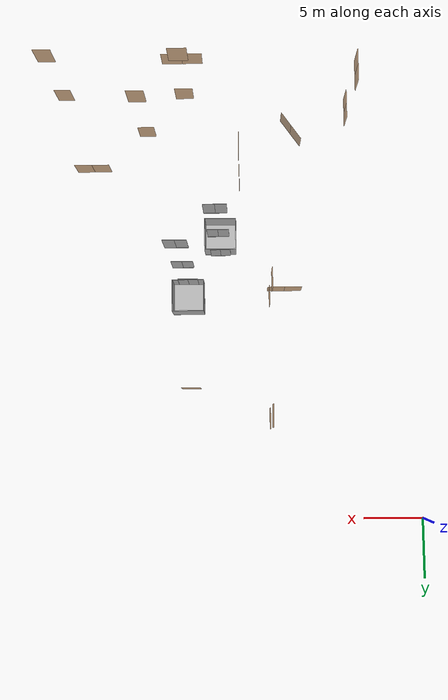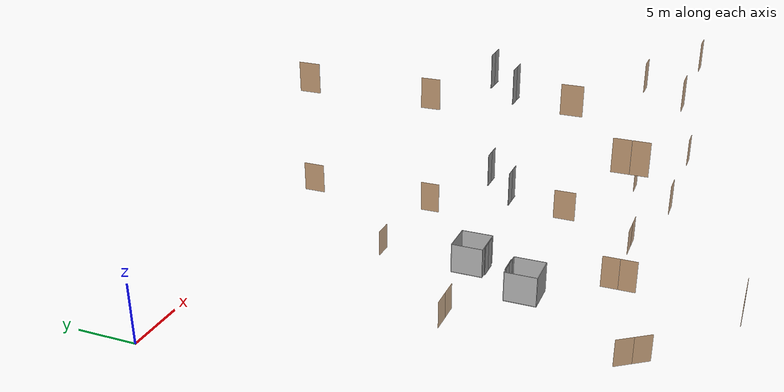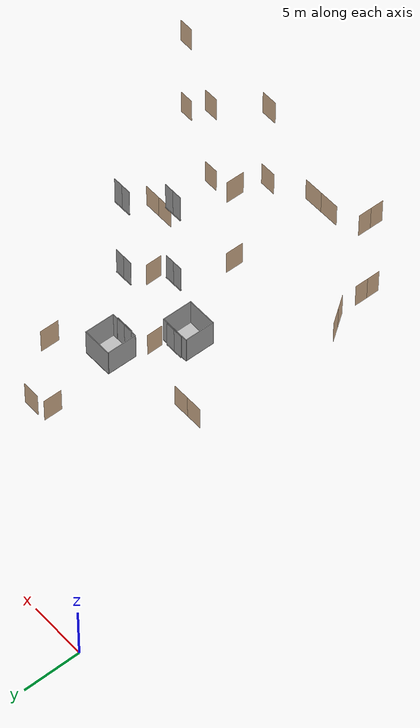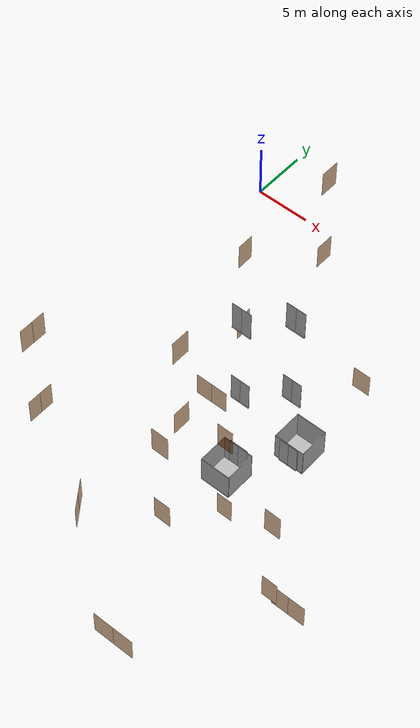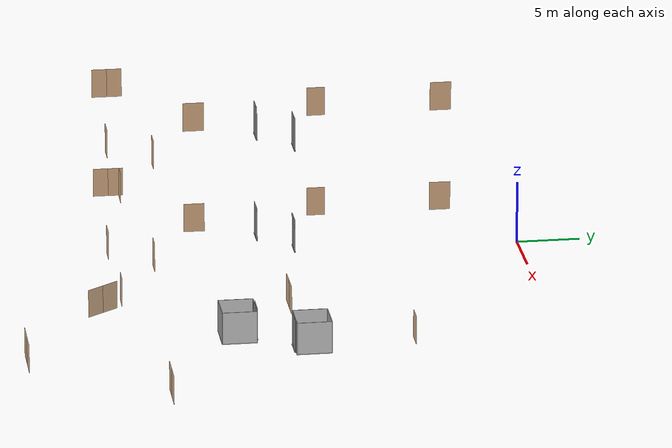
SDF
<sdf version="1.7">
 <world name="sim_world">
  <physics name="10ms" type="ode">
   <max_step_size>0.01</max_step_size>
   <real_time_factor>1.0</real_time_factor>
  </physics>
  <plugin filename="libgz-sim-physics-system.so" name="gz::sim::systems::Physics"/>
  <plugin filename="libgz-sim-user-commands-system.so" name="gz::sim::systems::UserCommands"/>
  <plugin filename="libgz-sim-scene-broadcaster-system.so" name="gz::sim::systems::SceneBroadcaster"/>
  <plugin filename="libdoor.so" name="door"/>
  <plugin filename="liblift.so" name="lift"/>
  <scene><ambient>1 1 1</ambient><background>0.8 0.8 0.8</background><grid>false</grid></scene>
  <light type="directional" name="sun">
   <pose>0 0 10 0 0 0</pose>
   <diffuse>1 1 1 1</diffuse>
   <specular>0.2 0.2 0.2 1</specular>
   <attenuation>
    <range>1000</range>
    <constant>0.09</constant>
    <linear>0.001</linear>
    <quadratic>0.001</quadratic>
   </attenuation>
   <direction>-0.5 0.1 -0.9</direction>
  </light>
  <model name="L1_door1">
   <pose>10.753654762321071 -33.79999264551465 0.0 0 0 2.1904910296829736</pose>
   <link name="right">
    <pose>0.7204413525969184 0 1.11 0 0 0</pose>
    <visual name="right_visual">
     <geometry><box><size>1.4308827051938369 0.03 2.2</size></box></geometry>
     <material>
      <ambient>0.5 0.25 0 0.6</ambient>
      <diffuse>0.5 0.25 0 0.6</diffuse>
      <pbr><metal><metalness>0.0</metalness></metal></pbr>
     </material>
    </visual>
    <collision name="right_collision">
     <geometry><box><size>1.4308827051938369 0.03 2.2</size></box></geometry>
     <surface><contact><collide_bitmask>0x02</collide_bitmask></contact></surface>
    </collision>
    <inertial>
     <mass>50.0</mass>
     <inertia><ixx>20.17041666666667</ixx><iyy>28.69760548342847</iyy><izz>8.534688816761804</izz></inertia>
    </inertial>
   </link>
   <joint name="right_joint" type="revolute">
    <parent>world</parent>
    <child>right</child>
    <axis><xyz>0 0 1</xyz><limit><lower>0</lower><upper>1.57</upper></limit></axis>
    <pose>0.7204413525969184 0 0 0 0 0</pose>
   </joint>
   <link name="left">
    <pose>-0.7204413525969184 0 1.11 0 0 0</pose>
    <visual name="left_visual">
     <geometry><box><size>1.4308827051938369 0.03 2.2</size></box></geometry>
     <material>
      <ambient>0.5 0.25 0 0.6</ambient>
      <diffuse>0.5 0.25 0 0.6</diffuse>
      <pbr><metal><metalness>0.0</metalness></metal></pbr>
     </material>
    </visual>
    <collision name="left_collision">
     <geometry><box><size>1.4308827051938369 0.03 2.2</size></box></geometry>
     <surface><contact><collide_bitmask>0x02</collide_bitmask></contact></surface>
    </collision>
    <inertial>
     <mass>50.0</mass>
     <inertia><ixx>20.17041666666667</ixx><iyy>28.69760548342847</iyy><izz>8.534688816761804</izz></inertia>
    </inertial>
   </link>
   <joint name="left_joint" type="revolute">
    <parent>world</parent>
    <child>left</child>
    <axis><xyz>0 0 1</xyz><limit><lower>-1.57</lower><upper>0</upper></limit></axis>
    <pose>-0.7204413525969184 0 0 0 0 0</pose>
   </joint>
   <plugin name="register_component" filename="libregister_component.so">
    <component name="Door">
     <v_max_door>0.5</v_max_door>
     <a_max_door>0.3</a_max_door>
     <a_nom_door>0.15</a_nom_door>
     <dx_min_door>0.01</dx_min_door>
     <f_max_door>500.0</f_max_door>
     <ros_interface>true</ros_interface>
     <door name="L1_door1" type="DoubleSwingDoor" left_joint_name="left_joint" right_joint_name="right_joint"/>
    </component>
   </plugin>
  </model>
  <model name="L1_door2">
   <pose>11.515053553551752 -19.600764056030513 0.0 0 0 -3.1369488994516814</pose>
   <link name="right">
    <pose>0.7374085791900343 0 1.11 0 0 0</pose>
    <visual name="right_visual">
     <geometry><box><size>1.4648171583800687 0.03 2.2</size></box></geometry>
     <material>
      <ambient>0.5 0.25 0 0.6</ambient>
      <diffuse>0.5 0.25 0 0.6</diffuse>
      <pbr><metal><metalness>0.0</metalness></metal></pbr>
     </material>
    </visual>
    <collision name="right_collision">
     <geometry><box><size>1.4648171583800687 0.03 2.2</size></box></geometry>
     <surface><contact><collide_bitmask>0x02</collide_bitmask></contact></surface>
    </collision>
    <inertial>
     <mass>50.0</mass>
     <inertia><ixx>20.17041666666667</ixx><iyy>29.107038781186084</iyy><izz>8.944122114519415</izz></inertia>
    </inertial>
   </link>
   <joint name="right_joint" type="prismatic">
    <parent>world</parent>
    <child>right</child>
    <axis>
     <xyz>1 0 0</xyz>
     <limit><lower>0.0</lower><upper>1.4748171583800687</upper><effort>500.0</effort></limit>
    </axis>
   </joint>
   <link name="left">
    <pose>-0.7374085791900343 0 1.11 0 0 0</pose>
    <visual name="left_visual">
     <geometry><box><size>1.4648171583800687 0.03 2.2</size></box></geometry>
     <material>
      <ambient>0.5 0.25 0 0.6</ambient>
      <diffuse>0.5 0.25 0 0.6</diffuse>
      <pbr><metal><metalness>0.0</metalness></metal></pbr>
     </material>
    </visual>
    <collision name="left_collision">
     <geometry><box><size>1.4648171583800687 0.03 2.2</size></box></geometry>
     <surface><contact><collide_bitmask>0x02</collide_bitmask></contact></surface>
    </collision>
    <inertial>
     <mass>50.0</mass>
     <inertia><ixx>20.17041666666667</ixx><iyy>29.107038781186084</iyy><izz>8.944122114519415</izz></inertia>
    </inertial>
   </link>
   <joint name="left_joint" type="prismatic">
    <parent>world</parent>
    <child>left</child>
    <axis>
     <xyz>1 0 0</xyz>
     <limit><lower>-1.4748171583800687</lower><upper>0.0</upper><effort>500.0</effort></limit>
    </axis>
   </joint>
   <plugin name="register_component" filename="libregister_component.so">
    <component name="Door">
     <v_max_door>0.2</v_max_door>
     <a_max_door>0.2</a_max_door>
     <a_nom_door>0.08</a_nom_door>
     <dx_min_door>0.001</dx_min_door>
     <f_max_door>100.0</f_max_door>
     <ros_interface>true</ros_interface>
     <door name="L1_door2" type="DoubleSlidingDoor" left_joint_name="left_joint" right_joint_name="right_joint"/>
    </component>
   </plugin>
  </model>
  <model name="L1_door3">
   <pose>20.334155710474544 -40.40725483879361 0.0 0 0 -3.137402798278724</pose>
   <link name="right">
    <pose>0.9069965354571369 0 1.11 0 0 0</pose>
    <visual name="right_visual">
     <geometry><box><size>1.8039930709142737 0.03 2.2</size></box></geometry>
     <material>
      <ambient>0.5 0.25 0 0.6</ambient>
      <diffuse>0.5 0.25 0 0.6</diffuse>
      <pbr><metal><metalness>0.0</metalness></metal></pbr>
     </material>
    </visual>
    <collision name="right_collision">
     <geometry><box><size>1.8039930709142737 0.03 2.2</size></box></geometry>
     <surface><contact><collide_bitmask>0x02</collide_bitmask></contact></surface>
    </collision>
    <inertial>
     <mass>50.0</mass>
     <inertia><ixx>20.17041666666667</ixx><iyy>33.726629166277974</iyy><izz>13.563712499611302</izz></inertia>
    </inertial>
   </link>
   <joint name="right_joint" type="prismatic">
    <parent>world</parent>
    <child>right</child>
    <axis>
     <xyz>1 0 0</xyz>
     <limit><lower>0.0</lower><upper>1.8139930709142738</upper><effort>500.0</effort></limit>
    </axis>
   </joint>
   <link name="left">
    <pose>-0.9069965354571369 0 1.11 0 0 0</pose>
    <visual name="left_visual">
     <geometry><box><size>1.8039930709142737 0.03 2.2</size></box></geometry>
     <material>
      <ambient>0.5 0.25 0 0.6</ambient>
      <diffuse>0.5 0.25 0 0.6</diffuse>
      <pbr><metal><metalness>0.0</metalness></metal></pbr>
     </material>
    </visual>
    <collision name="left_collision">
     <geometry><box><size>1.8039930709142737 0.03 2.2</size></box></geometry>
     <surface><contact><collide_bitmask>0x02</collide_bitmask></contact></surface>
    </collision>
    <inertial>
     <mass>50.0</mass>
     <inertia><ixx>20.17041666666667</ixx><iyy>33.726629166277974</iyy><izz>13.563712499611302</izz></inertia>
    </inertial>
   </link>
   <joint name="left_joint" type="prismatic">
    <parent>world</parent>
    <child>left</child>
    <axis>
     <xyz>1 0 0</xyz>
     <limit><lower>-1.8139930709142738</lower><upper>0.0</upper><effort>500.0</effort></limit>
    </axis>
   </joint>
   <plugin name="register_component" filename="libregister_component.so">
    <component name="Door">
     <v_max_door>0.2</v_max_door>
     <a_max_door>0.2</a_max_door>
     <a_nom_door>0.08</a_nom_door>
     <dx_min_door>0.001</dx_min_door>
     <f_max_door>100.0</f_max_door>
     <ros_interface>true</ros_interface>
     <door name="L1_door3" type="DoubleSlidingDoor" left_joint_name="left_joint" right_joint_name="right_joint"/>
    </component>
   </plugin>
  </model>
  <model name="L1_door4">
   <pose>19.549120677562087 -11.10939551168469 0.0 0 0 -0.009497018345977264</pose>
   <link name="right">
    <pose>0 0 1.11 0 0 0</pose>
    <visual name="right_visual">
     <geometry><box><size>1.5905993122484277 0.03 2.2</size></box></geometry>
     <material>
      <ambient>0.5 0.25 0 0.6</ambient>
      <diffuse>0.5 0.25 0 0.6</diffuse>
      <pbr><metal><metalness>0.0</metalness></metal></pbr>
     </material>
    </visual>
    <collision name="right_collision">
     <geometry><box><size>1.5905993122484277 0.03 2.2</size></box></geometry>
     <surface><contact><collide_bitmask>0x02</collide_bitmask></contact></surface>
    </collision>
    <inertial>
     <mass>50.0</mass>
     <inertia><ixx>20.17041666666667</ixx><iyy>30.70835905052155</iyy><izz>10.545442383854882</izz></inertia>
    </inertial>
   </link>
   <joint name="right_joint" type="revolute">
    <parent>world</parent>
    <child>right</child>
    <axis><xyz>0 0 1</xyz><limit><lower>0</lower><upper>1.57</upper></limit></axis>
    <pose>0.8002996561242138 0 0 0 0 0</pose>
   </joint>
   <plugin name="register_component" filename="libregister_component.so">
    <component name="Door">
     <v_max_door>0.5</v_max_door>
     <a_max_door>0.3</a_max_door>
     <a_nom_door>0.15</a_nom_door>
     <dx_min_door>0.01</dx_min_door>
     <f_max_door>500.0</f_max_door>
     <ros_interface>true</ros_interface>
     <door name="L1_door4" type="SwingDoor" left_joint_name="empty_joint" right_joint_name="right_joint"/>
    </component>
   </plugin>
  </model>
  <model name="L1_door5">
   <pose>28.079493196697264 -30.43738230505557 0.0 0 0 -0.0023958500301941633</pose>
   <link name="right">
    <pose>0.7494993011996198 0 1.11 0 0 0</pose>
    <visual name="right_visual">
     <geometry><box><size>1.4889986023992396 0.03 2.2</size></box></geometry>
     <material>
      <ambient>0.5 0.25 0 0.6</ambient>
      <diffuse>0.5 0.25 0 0.6</diffuse>
      <pbr><metal><metalness>0.0</metalness></metal></pbr>
     </material>
    </visual>
    <collision name="right_collision">
     <geometry><box><size>1.4889986023992396 0.03 2.2</size></box></geometry>
     <surface><contact><collide_bitmask>0x02</collide_bitmask></contact></surface>
    </collision>
    <inertial>
     <mass>50.0</mass>
     <inertia><ixx>20.17041666666667</ixx><iyy>29.404653491445373</iyy><izz>9.241736824778705</izz></inertia>
    </inertial>
   </link>
   <joint name="right_joint" type="prismatic">
    <parent>world</parent>
    <child>right</child>
    <axis>
     <xyz>1 0 0</xyz>
     <limit><lower>0.0</lower><upper>1.4989986023992397</upper><effort>500.0</effort></limit>
    </axis>
   </joint>
   <link name="left">
    <pose>-0.7494993011996198 0 1.11 0 0 0</pose>
    <visual name="left_visual">
     <geometry><box><size>1.4889986023992396 0.03 2.2</size></box></geometry>
     <material>
      <ambient>0.5 0.25 0 0.6</ambient>
      <diffuse>0.5 0.25 0 0.6</diffuse>
      <pbr><metal><metalness>0.0</metalness></metal></pbr>
     </material>
    </visual>
    <collision name="left_collision">
     <geometry><box><size>1.4889986023992396 0.03 2.2</size></box></geometry>
     <surface><contact><collide_bitmask>0x02</collide_bitmask></contact></surface>
    </collision>
    <inertial>
     <mass>50.0</mass>
     <inertia><ixx>20.17041666666667</ixx><iyy>29.404653491445373</iyy><izz>9.241736824778705</izz></inertia>
    </inertial>
   </link>
   <joint name="left_joint" type="prismatic">
    <parent>world</parent>
    <child>left</child>
    <axis>
     <xyz>1 0 0</xyz>
     <limit><lower>-1.4989986023992397</lower><upper>0.0</upper><effort>500.0</effort></limit>
    </axis>
   </joint>
   <plugin name="register_component" filename="libregister_component.so">
    <component name="Door">
     <v_max_door>0.2</v_max_door>
     <a_max_door>0.2</a_max_door>
     <a_nom_door>0.08</a_nom_door>
     <dx_min_door>0.001</dx_min_door>
     <f_max_door>100.0</f_max_door>
     <ros_interface>true</ros_interface>
     <door name="L1_door5" type="DoubleSlidingDoor" left_joint_name="left_joint" right_joint_name="right_joint"/>
    </component>
   </plugin>
  </model>
  <model name="L2_door2">
   <pose>6.76857286388343 -32.90682600516501 8.0 0 0 1.571612558028263</pose>
   <link name="right">
    <pose>0.5675078680191911 0 1.11 0 0 0</pose>
    <visual name="right_visual">
     <geometry><box><size>1.1250157360383821 0.03 2.2</size></box></geometry>
     <material>
      <ambient>0.5 0.25 0 0.6</ambient>
      <diffuse>0.5 0.25 0 0.6</diffuse>
      <pbr><metal><metalness>0.0</metalness></metal></pbr>
     </material>
    </visual>
    <collision name="right_collision">
     <geometry><box><size>1.1250157360383821 0.03 2.2</size></box></geometry>
     <surface><contact><collide_bitmask>0x02</collide_bitmask></contact></surface>
    </collision>
    <inertial>
     <mass>50.0</mass>
     <inertia><ixx>20.17041666666667</ixx><iyy>25.44025169305827</iyy><izz>5.277335026391595</izz></inertia>
    </inertial>
   </link>
   <joint name="right_joint" type="revolute">
    <parent>world</parent>
    <child>right</child>
    <axis><xyz>0 0 -1</xyz><limit><lower>0</lower><upper>1.57</upper></limit></axis>
    <pose>0.5675078680191911 0 0 0 0 0</pose>
   </joint>
   <link name="left">
    <pose>-0.5675078680191911 0 1.11 0 0 0</pose>
    <visual name="left_visual">
     <geometry><box><size>1.1250157360383821 0.03 2.2</size></box></geometry>
     <material>
      <ambient>0.5 0.25 0 0.6</ambient>
      <diffuse>0.5 0.25 0 0.6</diffuse>
      <pbr><metal><metalness>0.0</metalness></metal></pbr>
     </material>
    </visual>
    <collision name="left_collision">
     <geometry><box><size>1.1250157360383821 0.03 2.2</size></box></geometry>
     <surface><contact><collide_bitmask>0x02</collide_bitmask></contact></surface>
    </collision>
    <inertial>
     <mass>50.0</mass>
     <inertia><ixx>20.17041666666667</ixx><iyy>25.44025169305827</iyy><izz>5.277335026391595</izz></inertia>
    </inertial>
   </link>
   <joint name="left_joint" type="revolute">
    <parent>world</parent>
    <child>left</child>
    <axis><xyz>0 0 -1</xyz><limit><lower>-1.57</lower><upper>0</upper></limit></axis>
    <pose>-0.5675078680191911 0 0 0 0 0</pose>
   </joint>
   <plugin name="register_component" filename="libregister_component.so">
    <component name="Door">
     <v_max_door>0.5</v_max_door>
     <a_max_door>0.3</a_max_door>
     <a_nom_door>0.15</a_nom_door>
     <dx_min_door>0.01</dx_min_door>
     <f_max_door>500.0</f_max_door>
     <ros_interface>true</ros_interface>
     <door name="L2_door2" type="DoubleSwingDoor" left_joint_name="left_joint" right_joint_name="right_joint"/>
    </component>
   </plugin>
  </model>
  <model name="L2_door5">
   <pose>19.62055855578882 -34.21478433126707 8.0 0 0 3.1365461417546308</pose>
   <link name="right">
    <pose>0 0 1.11 0 0 0</pose>
    <visual name="right_visual">
     <geometry><box><size>1.4278667928054123 0.03 2.2</size></box></geometry>
     <material>
      <ambient>0.5 0.25 0 0.6</ambient>
      <diffuse>0.5 0.25 0 0.6</diffuse>
      <pbr><metal><metalness>0.0</metalness></metal></pbr>
     </material>
    </visual>
    <collision name="right_collision">
     <geometry><box><size>1.4278667928054123 0.03 2.2</size></box></geometry>
     <surface><contact><collide_bitmask>0x02</collide_bitmask></contact></surface>
    </collision>
    <inertial>
     <mass>50.0</mass>
     <inertia><ixx>20.17041666666667</ixx><iyy>28.661681574985064</iyy><izz>8.498764908318392</izz></inertia>
    </inertial>
   </link>
   <joint name="right_joint" type="revolute">
    <parent>world</parent>
    <child>right</child>
    <axis><xyz>0 0 -1</xyz><limit><lower>0</lower><upper>1.57</upper></limit></axis>
    <pose>0.7189333964027061 0 0 0 0 0</pose>
   </joint>
   <plugin name="register_component" filename="libregister_component.so">
    <component name="Door">
     <v_max_door>0.5</v_max_door>
     <a_max_door>0.3</a_max_door>
     <a_nom_door>0.15</a_nom_door>
     <dx_min_door>0.01</dx_min_door>
     <f_max_door>500.0</f_max_door>
     <ros_interface>true</ros_interface>
     <door name="L2_door5" type="SwingDoor" left_joint_name="empty_joint" right_joint_name="right_joint"/>
    </component>
   </plugin>
  </model>
  <model name="L2_door9">
   <pose>13.018848337594756 -17.76158217016259 8.0 0 0 1.5874688733681936</pose>
   <link name="right">
    <pose>0 0 1.11 0 0 0</pose>
    <visual name="right_visual">
     <geometry><box><size>1.382945881897145 0.03 2.2</size></box></geometry>
     <material>
      <ambient>0.5 0.25 0 0.6</ambient>
      <diffuse>0.5 0.25 0 0.6</diffuse>
      <pbr><metal><metalness>0.0</metalness></metal></pbr>
     </material>
    </visual>
    <collision name="right_collision">
     <geometry><box><size>1.382945881897145 0.03 2.2</size></box></geometry>
     <surface><contact><collide_bitmask>0x02</collide_bitmask></contact></surface>
    </collision>
    <inertial>
     <mass>50.0</mass>
     <inertia><ixx>20.17041666666667</ixx><iyy>28.13558046773447</iyy><izz>7.9726638010677995</izz></inertia>
    </inertial>
   </link>
   <joint name="right_joint" type="revolute">
    <parent>world</parent>
    <child>right</child>
    <axis><xyz>0 0 -1</xyz><limit><lower>0</lower><upper>1.57</upper></limit></axis>
    <pose>0.6964729409485725 0 0 0 0 0</pose>
   </joint>
   <plugin name="register_component" filename="libregister_component.so">
    <component name="Door">
     <v_max_door>0.5</v_max_door>
     <a_max_door>0.3</a_max_door>
     <a_nom_door>0.15</a_nom_door>
     <dx_min_door>0.01</dx_min_door>
     <f_max_door>500.0</f_max_door>
     <ros_interface>true</ros_interface>
     <door name="L2_door9" type="SwingDoor" left_joint_name="empty_joint" right_joint_name="right_joint"/>
    </component>
   </plugin>
  </model>
  <model name="L2_door11">
   <pose>13.070832545372092 -8.29507317951618 8.0 0 0 1.571612558028263</pose>
   <link name="right">
    <pose>0 0 1.11 0 0 0</pose>
    <visual name="right_visual">
     <geometry><box><size>1.5950330216253457 0.03 2.2</size></box></geometry>
     <material>
      <ambient>0.5 0.25 0 0.6</ambient>
      <diffuse>0.5 0.25 0 0.6</diffuse>
      <pbr><metal><metalness>0.0</metalness></metal></pbr>
     </material>
    </visual>
    <collision name="right_collision">
     <geometry><box><size>1.5950330216253457 0.03 2.2</size></box></geometry>
     <surface><contact><collide_bitmask>0x02</collide_bitmask></contact></surface>
    </collision>
    <inertial>
     <mass>50.0</mass>
     <inertia><ixx>20.17041666666667</ixx><iyy>30.767209750313672</iyy><izz>10.604293083647002</izz></inertia>
    </inertial>
   </link>
   <joint name="right_joint" type="revolute">
    <parent>world</parent>
    <child>right</child>
    <axis><xyz>0 0 -1</xyz><limit><lower>0</lower><upper>1.57</upper></limit></axis>
    <pose>0.8025165108126728 0 0 0 0 0</pose>
   </joint>
   <plugin name="register_component" filename="libregister_component.so">
    <component name="Door">
     <v_max_door>0.5</v_max_door>
     <a_max_door>0.3</a_max_door>
     <a_nom_door>0.15</a_nom_door>
     <dx_min_door>0.01</dx_min_door>
     <f_max_door>500.0</f_max_door>
     <ros_interface>true</ros_interface>
     <door name="L2_door11" type="SwingDoor" left_joint_name="empty_joint" right_joint_name="right_joint"/>
    </component>
   </plugin>
  </model>
  <model name="L2_door12">
   <pose>15.28470442617677 -27.2761317707633 8.0 0 0 1.571612558028262</pose>
   <link name="right">
    <pose>0 0 1.11 0 0 0</pose>
    <visual name="right_visual">
     <geometry><box><size>1.5658659299508506 0.03 2.2</size></box></geometry>
     <material>
      <ambient>0.5 0.25 0 0.6</ambient>
      <diffuse>0.5 0.25 0 0.6</diffuse>
      <pbr><metal><metalness>0.0</metalness></metal></pbr>
     </material>
    </visual>
    <collision name="right_collision">
     <geometry><box><size>1.5658659299508506 0.03 2.2</size></box></geometry>
     <surface><contact><collide_bitmask>0x02</collide_bitmask></contact></surface>
    </collision>
    <inertial>
     <mass>50.0</mass>
     <inertia><ixx>20.17041666666667</ixx><iyy>30.38306712742018</iyy><izz>10.22015046075351</izz></inertia>
    </inertial>
   </link>
   <joint name="right_joint" type="revolute">
    <parent>world</parent>
    <child>right</child>
    <axis><xyz>0 0 1</xyz><limit><lower>0</lower><upper>1.57</upper></limit></axis>
    <pose>0.7879329649754253 0 0 0 0 0</pose>
   </joint>
   <plugin name="register_component" filename="libregister_component.so">
    <component name="Door">
     <v_max_door>0.5</v_max_door>
     <a_max_door>0.3</a_max_door>
     <a_nom_door>0.15</a_nom_door>
     <dx_min_door>0.01</dx_min_door>
     <f_max_door>500.0</f_max_door>
     <ros_interface>true</ros_interface>
     <door name="L2_door12" type="SwingDoor" left_joint_name="empty_joint" right_joint_name="right_joint"/>
    </component>
   </plugin>
  </model>
  <model name="L2_door14">
   <pose>22.582882547846204 -31.092638612981972 8.0 0 0 3.137779488569298</pose>
   <link name="right">
    <pose>0 0 1.11 0 0 0</pose>
    <visual name="right_visual">
     <geometry><box><size>1.2889329745237348 0.03 2.2</size></box></geometry>
     <material>
      <ambient>0.5 0.25 0 0.6</ambient>
      <diffuse>0.5 0.25 0 0.6</diffuse>
      <pbr><metal><metalness>0.0</metalness></metal></pbr>
     </material>
    </visual>
    <collision name="right_collision">
     <geometry><box><size>1.2889329745237348 0.03 2.2</size></box></geometry>
     <surface><contact><collide_bitmask>0x02</collide_bitmask></contact></surface>
    </collision>
    <inertial>
     <mass>50.0</mass>
     <inertia><ixx>20.17041666666667</ixx><iyy>27.088950886727517</iyy><izz>6.926034220060845</izz></inertia>
    </inertial>
   </link>
   <joint name="right_joint" type="revolute">
    <parent>world</parent>
    <child>right</child>
    <axis><xyz>0 0 1</xyz><limit><lower>0</lower><upper>1.57</upper></limit></axis>
    <pose>0.6494664872618674 0 0 0 0 0</pose>
   </joint>
   <plugin name="register_component" filename="libregister_component.so">
    <component name="Door">
     <v_max_door>0.5</v_max_door>
     <a_max_door>0.3</a_max_door>
     <a_nom_door>0.15</a_nom_door>
     <dx_min_door>0.01</dx_min_door>
     <f_max_door>500.0</f_max_door>
     <ros_interface>true</ros_interface>
     <door name="L2_door14" type="SwingDoor" left_joint_name="empty_joint" right_joint_name="right_joint"/>
    </component>
   </plugin>
  </model>
  <model name="L2_door15">
   <pose>29.19689685453295 -34.1844883615378 8.0 0 0 3.1287318603676484</pose>
   <link name="right">
    <pose>0 0 1.11 0 0 0</pose>
    <visual name="right_visual">
     <geometry><box><size>1.2884785147293154 0.03 2.2</size></box></geometry>
     <material>
      <ambient>0.5 0.25 0 0.6</ambient>
      <diffuse>0.5 0.25 0 0.6</diffuse>
      <pbr><metal><metalness>0.0</metalness></metal></pbr>
     </material>
    </visual>
    <collision name="right_collision">
     <geometry><box><size>1.2884785147293154 0.03 2.2</size></box></geometry>
     <surface><contact><collide_bitmask>0x02</collide_bitmask></contact></surface>
    </collision>
    <inertial>
     <mass>50.0</mass>
     <inertia><ixx>20.17041666666667</ixx><iyy>27.0840703454961</iyy><izz>6.921153678829428</izz></inertia>
    </inertial>
   </link>
   <joint name="right_joint" type="revolute">
    <parent>world</parent>
    <child>right</child>
    <axis><xyz>0 0 -1</xyz><limit><lower>0</lower><upper>1.57</upper></limit></axis>
    <pose>0.6492392573646577 0 0 0 0 0</pose>
   </joint>
   <plugin name="register_component" filename="libregister_component.so">
    <component name="Door">
     <v_max_door>0.5</v_max_door>
     <a_max_door>0.3</a_max_door>
     <a_nom_door>0.15</a_nom_door>
     <dx_min_door>0.01</dx_min_door>
     <f_max_door>500.0</f_max_door>
     <ros_interface>true</ros_interface>
     <door name="L2_door15" type="SwingDoor" left_joint_name="empty_joint" right_joint_name="right_joint"/>
    </component>
   </plugin>
  </model>
  <model name="L3_door2">
   <pose>6.76857286388343 -32.90682600516501 16.0 0 0 1.571612558028263</pose>
   <link name="right">
    <pose>0.5675078680191911 0 1.11 0 0 0</pose>
    <visual name="right_visual">
     <geometry><box><size>1.1250157360383821 0.03 2.2</size></box></geometry>
     <material>
      <ambient>0.5 0.25 0 0.6</ambient>
      <diffuse>0.5 0.25 0 0.6</diffuse>
      <pbr><metal><metalness>0.0</metalness></metal></pbr>
     </material>
    </visual>
    <collision name="right_collision">
     <geometry><box><size>1.1250157360383821 0.03 2.2</size></box></geometry>
     <surface><contact><collide_bitmask>0x02</collide_bitmask></contact></surface>
    </collision>
    <inertial>
     <mass>50.0</mass>
     <inertia><ixx>20.17041666666667</ixx><iyy>25.44025169305827</iyy><izz>5.277335026391595</izz></inertia>
    </inertial>
   </link>
   <joint name="right_joint" type="revolute">
    <parent>world</parent>
    <child>right</child>
    <axis><xyz>0 0 -1</xyz><limit><lower>0</lower><upper>1.57</upper></limit></axis>
    <pose>0.5675078680191911 0 0 0 0 0</pose>
   </joint>
   <link name="left">
    <pose>-0.5675078680191911 0 1.11 0 0 0</pose>
    <visual name="left_visual">
     <geometry><box><size>1.1250157360383821 0.03 2.2</size></box></geometry>
     <material>
      <ambient>0.5 0.25 0 0.6</ambient>
      <diffuse>0.5 0.25 0 0.6</diffuse>
      <pbr><metal><metalness>0.0</metalness></metal></pbr>
     </material>
    </visual>
    <collision name="left_collision">
     <geometry><box><size>1.1250157360383821 0.03 2.2</size></box></geometry>
     <surface><contact><collide_bitmask>0x02</collide_bitmask></contact></surface>
    </collision>
    <inertial>
     <mass>50.0</mass>
     <inertia><ixx>20.17041666666667</ixx><iyy>25.44025169305827</iyy><izz>5.277335026391595</izz></inertia>
    </inertial>
   </link>
   <joint name="left_joint" type="revolute">
    <parent>world</parent>
    <child>left</child>
    <axis><xyz>0 0 -1</xyz><limit><lower>-1.57</lower><upper>0</upper></limit></axis>
    <pose>-0.5675078680191911 0 0 0 0 0</pose>
   </joint>
   <plugin name="register_component" filename="libregister_component.so">
    <component name="Door">
     <v_max_door>0.5</v_max_door>
     <a_max_door>0.3</a_max_door>
     <a_nom_door>0.15</a_nom_door>
     <dx_min_door>0.01</dx_min_door>
     <f_max_door>500.0</f_max_door>
     <ros_interface>true</ros_interface>
     <door name="L3_door2" type="DoubleSwingDoor" left_joint_name="left_joint" right_joint_name="right_joint"/>
    </component>
   </plugin>
  </model>
  <model name="L3_door5">
   <pose>19.62055855578882 -34.21478433126707 16.0 0 0 3.1365461417546308</pose>
   <link name="right">
    <pose>0 0 1.11 0 0 0</pose>
    <visual name="right_visual">
     <geometry><box><size>1.4278667928054123 0.03 2.2</size></box></geometry>
     <material>
      <ambient>0.5 0.25 0 0.6</ambient>
      <diffuse>0.5 0.25 0 0.6</diffuse>
      <pbr><metal><metalness>0.0</metalness></metal></pbr>
     </material>
    </visual>
    <collision name="right_collision">
     <geometry><box><size>1.4278667928054123 0.03 2.2</size></box></geometry>
     <surface><contact><collide_bitmask>0x02</collide_bitmask></contact></surface>
    </collision>
    <inertial>
     <mass>50.0</mass>
     <inertia><ixx>20.17041666666667</ixx><iyy>28.661681574985064</iyy><izz>8.498764908318392</izz></inertia>
    </inertial>
   </link>
   <joint name="right_joint" type="revolute">
    <parent>world</parent>
    <child>right</child>
    <axis><xyz>0 0 -1</xyz><limit><lower>0</lower><upper>1.57</upper></limit></axis>
    <pose>0.7189333964027061 0 0 0 0 0</pose>
   </joint>
   <plugin name="register_component" filename="libregister_component.so">
    <component name="Door">
     <v_max_door>0.5</v_max_door>
     <a_max_door>0.3</a_max_door>
     <a_nom_door>0.15</a_nom_door>
     <dx_min_door>0.01</dx_min_door>
     <f_max_door>500.0</f_max_door>
     <ros_interface>true</ros_interface>
     <door name="L3_door5" type="SwingDoor" left_joint_name="empty_joint" right_joint_name="right_joint"/>
    </component>
   </plugin>
  </model>
  <model name="L3_door9">
   <pose>13.018848337594756 -17.76158217016259 16.0 0 0 1.5874688733681936</pose>
   <link name="right">
    <pose>0 0 1.11 0 0 0</pose>
    <visual name="right_visual">
     <geometry><box><size>1.382945881897145 0.03 2.2</size></box></geometry>
     <material>
      <ambient>0.5 0.25 0 0.6</ambient>
      <diffuse>0.5 0.25 0 0.6</diffuse>
      <pbr><metal><metalness>0.0</metalness></metal></pbr>
     </material>
    </visual>
    <collision name="right_collision">
     <geometry><box><size>1.382945881897145 0.03 2.2</size></box></geometry>
     <surface><contact><collide_bitmask>0x02</collide_bitmask></contact></surface>
    </collision>
    <inertial>
     <mass>50.0</mass>
     <inertia><ixx>20.17041666666667</ixx><iyy>28.13558046773447</iyy><izz>7.9726638010677995</izz></inertia>
    </inertial>
   </link>
   <joint name="right_joint" type="revolute">
    <parent>world</parent>
    <child>right</child>
    <axis><xyz>0 0 -1</xyz><limit><lower>0</lower><upper>1.57</upper></limit></axis>
    <pose>0.6964729409485725 0 0 0 0 0</pose>
   </joint>
   <plugin name="register_component" filename="libregister_component.so">
    <component name="Door">
     <v_max_door>0.5</v_max_door>
     <a_max_door>0.3</a_max_door>
     <a_nom_door>0.15</a_nom_door>
     <dx_min_door>0.01</dx_min_door>
     <f_max_door>500.0</f_max_door>
     <ros_interface>true</ros_interface>
     <door name="L3_door9" type="SwingDoor" left_joint_name="empty_joint" right_joint_name="right_joint"/>
    </component>
   </plugin>
  </model>
  <model name="L3_door11">
   <pose>13.070832545372092 -8.29507317951618 16.0 0 0 1.571612558028263</pose>
   <link name="right">
    <pose>0 0 1.11 0 0 0</pose>
    <visual name="right_visual">
     <geometry><box><size>1.5950330216253457 0.03 2.2</size></box></geometry>
     <material>
      <ambient>0.5 0.25 0 0.6</ambient>
      <diffuse>0.5 0.25 0 0.6</diffuse>
      <pbr><metal><metalness>0.0</metalness></metal></pbr>
     </material>
    </visual>
    <collision name="right_collision">
     <geometry><box><size>1.5950330216253457 0.03 2.2</size></box></geometry>
     <surface><contact><collide_bitmask>0x02</collide_bitmask></contact></surface>
    </collision>
    <inertial>
     <mass>50.0</mass>
     <inertia><ixx>20.17041666666667</ixx><iyy>30.767209750313672</iyy><izz>10.604293083647002</izz></inertia>
    </inertial>
   </link>
   <joint name="right_joint" type="revolute">
    <parent>world</parent>
    <child>right</child>
    <axis><xyz>0 0 -1</xyz><limit><lower>0</lower><upper>1.57</upper></limit></axis>
    <pose>0.8025165108126728 0 0 0 0 0</pose>
   </joint>
   <plugin name="register_component" filename="libregister_component.so">
    <component name="Door">
     <v_max_door>0.5</v_max_door>
     <a_max_door>0.3</a_max_door>
     <a_nom_door>0.15</a_nom_door>
     <dx_min_door>0.01</dx_min_door>
     <f_max_door>500.0</f_max_door>
     <ros_interface>true</ros_interface>
     <door name="L3_door11" type="SwingDoor" left_joint_name="empty_joint" right_joint_name="right_joint"/>
    </component>
   </plugin>
  </model>
  <model name="L3_door12">
   <pose>15.28470442617677 -27.2761317707633 16.0 0 0 1.571612558028262</pose>
   <link name="right">
    <pose>0 0 1.11 0 0 0</pose>
    <visual name="right_visual">
     <geometry><box><size>1.5658659299508506 0.03 2.2</size></box></geometry>
     <material>
      <ambient>0.5 0.25 0 0.6</ambient>
      <diffuse>0.5 0.25 0 0.6</diffuse>
      <pbr><metal><metalness>0.0</metalness></metal></pbr>
     </material>
    </visual>
    <collision name="right_collision">
     <geometry><box><size>1.5658659299508506 0.03 2.2</size></box></geometry>
     <surface><contact><collide_bitmask>0x02</collide_bitmask></contact></surface>
    </collision>
    <inertial>
     <mass>50.0</mass>
     <inertia><ixx>20.17041666666667</ixx><iyy>30.38306712742018</iyy><izz>10.22015046075351</izz></inertia>
    </inertial>
   </link>
   <joint name="right_joint" type="revolute">
    <parent>world</parent>
    <child>right</child>
    <axis><xyz>0 0 1</xyz><limit><lower>0</lower><upper>1.57</upper></limit></axis>
    <pose>0.7879329649754253 0 0 0 0 0</pose>
   </joint>
   <plugin name="register_component" filename="libregister_component.so">
    <component name="Door">
     <v_max_door>0.5</v_max_door>
     <a_max_door>0.3</a_max_door>
     <a_nom_door>0.15</a_nom_door>
     <dx_min_door>0.01</dx_min_door>
     <f_max_door>500.0</f_max_door>
     <ros_interface>true</ros_interface>
     <door name="L3_door12" type="SwingDoor" left_joint_name="empty_joint" right_joint_name="right_joint"/>
    </component>
   </plugin>
  </model>
  <model name="L3_door14">
   <pose>22.582882547846204 -31.092638612981972 16.0 0 0 3.137779488569298</pose>
   <link name="right">
    <pose>0 0 1.11 0 0 0</pose>
    <visual name="right_visual">
     <geometry><box><size>1.2889329745237348 0.03 2.2</size></box></geometry>
     <material>
      <ambient>0.5 0.25 0 0.6</ambient>
      <diffuse>0.5 0.25 0 0.6</diffuse>
      <pbr><metal><metalness>0.0</metalness></metal></pbr>
     </material>
    </visual>
    <collision name="right_collision">
     <geometry><box><size>1.2889329745237348 0.03 2.2</size></box></geometry>
     <surface><contact><collide_bitmask>0x02</collide_bitmask></contact></surface>
    </collision>
    <inertial>
     <mass>50.0</mass>
     <inertia><ixx>20.17041666666667</ixx><iyy>27.088950886727517</iyy><izz>6.926034220060845</izz></inertia>
    </inertial>
   </link>
   <joint name="right_joint" type="revolute">
    <parent>world</parent>
    <child>right</child>
    <axis><xyz>0 0 1</xyz><limit><lower>0</lower><upper>1.57</upper></limit></axis>
    <pose>0.6494664872618674 0 0 0 0 0</pose>
   </joint>
   <plugin name="register_component" filename="libregister_component.so">
    <component name="Door">
     <v_max_door>0.5</v_max_door>
     <a_max_door>0.3</a_max_door>
     <a_nom_door>0.15</a_nom_door>
     <dx_min_door>0.01</dx_min_door>
     <f_max_door>500.0</f_max_door>
     <ros_interface>true</ros_interface>
     <door name="L3_door14" type="SwingDoor" left_joint_name="empty_joint" right_joint_name="right_joint"/>
    </component>
   </plugin>
  </model>
  <model name="L3_door15">
   <pose>29.19689685453295 -34.1844883615378 16.0 0 0 3.1287318603676484</pose>
   <link name="right">
    <pose>0 0 1.11 0 0 0</pose>
    <visual name="right_visual">
     <geometry><box><size>1.2884785147293154 0.03 2.2</size></box></geometry>
     <material>
      <ambient>0.5 0.25 0 0.6</ambient>
      <diffuse>0.5 0.25 0 0.6</diffuse>
      <pbr><metal><metalness>0.0</metalness></metal></pbr>
     </material>
    </visual>
    <collision name="right_collision">
     <geometry><box><size>1.2884785147293154 0.03 2.2</size></box></geometry>
     <surface><contact><collide_bitmask>0x02</collide_bitmask></contact></surface>
    </collision>
    <inertial>
     <mass>50.0</mass>
     <inertia><ixx>20.17041666666667</ixx><iyy>27.0840703454961</iyy><izz>6.921153678829428</izz></inertia>
    </inertial>
   </link>
   <joint name="right_joint" type="revolute">
    <parent>world</parent>
    <child>right</child>
    <axis><xyz>0 0 -1</xyz><limit><lower>0</lower><upper>1.57</upper></limit></axis>
    <pose>0.6492392573646577 0 0 0 0 0</pose>
   </joint>
   <plugin name="register_component" filename="libregister_component.so">
    <component name="Door">
     <v_max_door>0.5</v_max_door>
     <a_max_door>0.3</a_max_door>
     <a_nom_door>0.15</a_nom_door>
     <dx_min_door>0.01</dx_min_door>
     <f_max_door>500.0</f_max_door>
     <ros_interface>true</ros_interface>
     <door name="L3_door15" type="SwingDoor" left_joint_name="empty_joint" right_joint_name="right_joint"/>
    </component>
   </plugin>
  </model>
  <model name="ShaftDoor_Lift1_L1_lift1_door">
   <pose>19.766468308668816 -20.331265422387034 0.0 0 0 0.0</pose>
   <link name="right_door">
    <pose>0.425 0 1.25 0 0 0</pose>
    <visual name="right_door_visual">
     <geometry><box><size>0.85 0.03 2.5</size></box></geometry>
     <material>
      <ambient>0.5 0.5 0.5 1</ambient>
      <diffuse>0.7 0.7 0.7 1</diffuse>
      <specular>0.6 0.6 0.6 1</specular>
      <emissive>0.1 0.1 0.1 1</emissive>
     </material>
    </visual>
    <collision name="right_door_collision">
     <geometry><box><size>0.85 0.03 2.5</size></box></geometry>
     <surface><contact><collide_bitmask>0x02</collide_bitmask></contact></surface>
    </collision>
   </link>
   <link name="left_door">
    <pose>-0.425 0 1.25 0 0 0</pose>
    <visual name="left_door_visual">
     <geometry><box><size>0.85 0.03 2.5</size></box></geometry>
     <material>
      <ambient>0.5 0.5 0.5 1</ambient>
      <diffuse>0.7 0.7 0.7 1</diffuse>
      <specular>0.6 0.6 0.6 1</specular>
      <emissive>0.1 0.1 0.1 1</emissive>
     </material>
    </visual>
    <collision name="left_door_collision">
     <geometry><box><size>0.85 0.03 2.5</size></box></geometry>
     <surface><contact><collide_bitmask>0x02</collide_bitmask></contact></surface>
    </collision>
   </link>
   <joint name="right_joint" type="prismatic">
    <parent>world</parent>
    <child>right_door</child>
    <axis><xyz>1 0 0</xyz><limit><lower>0</lower><upper>0.85</upper></limit></axis>
   </joint>
   <joint name="left_joint" type="prismatic">
    <parent>world</parent>
    <child>left_door</child>
    <axis><xyz>1 0 0</xyz><limit><lower>-0.85</lower><upper>0</upper></limit></axis>
   </joint>
   <link name="ramp">
    <pose>0 0 -0.025 0 0 0</pose>
    <visual name="ramp_visual">
     <geometry><box><size>1.7 0.1 0.05</size></box></geometry>
     <material>
      <ambient>0.5 0.5 0.5 1</ambient>
      <diffuse>0.7 0.7 0.7 1</diffuse>
      <specular>0.6 0.6 0.6 1</specular>
      <emissive>0.1 0.1 0.1 1</emissive>
     </material>
    </visual>
    <collision name="ramp_collision">
     <geometry><box><size>1.7 0.1 0.05</size></box></geometry>
     <surface><contact><collide_bitmask>0x02</collide_bitmask></contact></surface>
    </collision>
   </link>
   <joint name="ramp_joint" type="fixed"><parent>world</parent><child>ramp</child></joint>
   <plugin name="register_component" filename="libregister_component.so">
    <component name="Door">
     <v_max_door>0.3</v_max_door>
     <a_max_door>0.2</a_max_door>
     <a_nom_door>0.1</a_nom_door>
     <dx_min_door>0.0001</dx_min_door>
     <f_max_door>35.0</f_max_door>
     <door left_joint_name="left_joint" name="ShaftDoor_Lift1_L1_lift1_door" right_joint_name="right_joint" type="DoubleSlidingDoor"/>
    </component>
   </plugin>
  </model>
  <model name="ShaftDoor_Lift1_L2_lift1_door">
   <pose>19.766468308668816 -20.331265422387034 8.0 0 0 0.0</pose>
   <link name="right_door">
    <pose>0.425 0 1.25 0 0 0</pose>
    <visual name="right_door_visual">
     <geometry><box><size>0.85 0.03 2.5</size></box></geometry>
     <material>
      <ambient>0.5 0.5 0.5 1</ambient>
      <diffuse>0.7 0.7 0.7 1</diffuse>
      <specular>0.6 0.6 0.6 1</specular>
      <emissive>0.1 0.1 0.1 1</emissive>
     </material>
    </visual>
    <collision name="right_door_collision">
     <geometry><box><size>0.85 0.03 2.5</size></box></geometry>
     <surface><contact><collide_bitmask>0x02</collide_bitmask></contact></surface>
    </collision>
   </link>
   <link name="left_door">
    <pose>-0.425 0 1.25 0 0 0</pose>
    <visual name="left_door_visual">
     <geometry><box><size>0.85 0.03 2.5</size></box></geometry>
     <material>
      <ambient>0.5 0.5 0.5 1</ambient>
      <diffuse>0.7 0.7 0.7 1</diffuse>
      <specular>0.6 0.6 0.6 1</specular>
      <emissive>0.1 0.1 0.1 1</emissive>
     </material>
    </visual>
    <collision name="left_door_collision">
     <geometry><box><size>0.85 0.03 2.5</size></box></geometry>
     <surface><contact><collide_bitmask>0x02</collide_bitmask></contact></surface>
    </collision>
   </link>
   <joint name="right_joint" type="prismatic">
    <parent>world</parent>
    <child>right_door</child>
    <axis><xyz>1 0 0</xyz><limit><lower>0</lower><upper>0.85</upper></limit></axis>
   </joint>
   <joint name="left_joint" type="prismatic">
    <parent>world</parent>
    <child>left_door</child>
    <axis><xyz>1 0 0</xyz><limit><lower>-0.85</lower><upper>0</upper></limit></axis>
   </joint>
   <link name="ramp">
    <pose>0 0 -0.025 0 0 0</pose>
    <visual name="ramp_visual">
     <geometry><box><size>1.7 0.1 0.05</size></box></geometry>
     <material>
      <ambient>0.5 0.5 0.5 1</ambient>
      <diffuse>0.7 0.7 0.7 1</diffuse>
      <specular>0.6 0.6 0.6 1</specular>
      <emissive>0.1 0.1 0.1 1</emissive>
     </material>
    </visual>
    <collision name="ramp_collision">
     <geometry><box><size>1.7 0.1 0.05</size></box></geometry>
     <surface><contact><collide_bitmask>0x02</collide_bitmask></contact></surface>
    </collision>
   </link>
   <joint name="ramp_joint" type="fixed"><parent>world</parent><child>ramp</child></joint>
   <plugin name="register_component" filename="libregister_component.so">
    <component name="Door">
     <v_max_door>0.3</v_max_door>
     <a_max_door>0.2</a_max_door>
     <a_nom_door>0.1</a_nom_door>
     <dx_min_door>0.0001</dx_min_door>
     <f_max_door>35.0</f_max_door>
     <door left_joint_name="left_joint" name="ShaftDoor_Lift1_L2_lift1_door" right_joint_name="right_joint" type="DoubleSlidingDoor"/>
    </component>
   </plugin>
  </model>
  <model name="ShaftDoor_Lift1_L3_lift1_door">
   <pose>19.766468308668816 -20.331265422387034 16.0 0 0 0.0</pose>
   <link name="right_door">
    <pose>0.425 0 1.25 0 0 0</pose>
    <visual name="right_door_visual">
     <geometry><box><size>0.85 0.03 2.5</size></box></geometry>
     <material>
      <ambient>0.5 0.5 0.5 1</ambient>
      <diffuse>0.7 0.7 0.7 1</diffuse>
      <specular>0.6 0.6 0.6 1</specular>
      <emissive>0.1 0.1 0.1 1</emissive>
     </material>
    </visual>
    <collision name="right_door_collision">
     <geometry><box><size>0.85 0.03 2.5</size></box></geometry>
     <surface><contact><collide_bitmask>0x02</collide_bitmask></contact></surface>
    </collision>
   </link>
   <link name="left_door">
    <pose>-0.425 0 1.25 0 0 0</pose>
    <visual name="left_door_visual">
     <geometry><box><size>0.85 0.03 2.5</size></box></geometry>
     <material>
      <ambient>0.5 0.5 0.5 1</ambient>
      <diffuse>0.7 0.7 0.7 1</diffuse>
      <specular>0.6 0.6 0.6 1</specular>
      <emissive>0.1 0.1 0.1 1</emissive>
     </material>
    </visual>
    <collision name="left_door_collision">
     <geometry><box><size>0.85 0.03 2.5</size></box></geometry>
     <surface><contact><collide_bitmask>0x02</collide_bitmask></contact></surface>
    </collision>
   </link>
   <joint name="right_joint" type="prismatic">
    <parent>world</parent>
    <child>right_door</child>
    <axis><xyz>1 0 0</xyz><limit><lower>0</lower><upper>0.85</upper></limit></axis>
   </joint>
   <joint name="left_joint" type="prismatic">
    <parent>world</parent>
    <child>left_door</child>
    <axis><xyz>1 0 0</xyz><limit><lower>-0.85</lower><upper>0</upper></limit></axis>
   </joint>
   <link name="ramp">
    <pose>0 0 -0.025 0 0 0</pose>
    <visual name="ramp_visual">
     <geometry><box><size>1.7 0.1 0.05</size></box></geometry>
     <material>
      <ambient>0.5 0.5 0.5 1</ambient>
      <diffuse>0.7 0.7 0.7 1</diffuse>
      <specular>0.6 0.6 0.6 1</specular>
      <emissive>0.1 0.1 0.1 1</emissive>
     </material>
    </visual>
    <collision name="ramp_collision">
     <geometry><box><size>1.7 0.1 0.05</size></box></geometry>
     <surface><contact><collide_bitmask>0x02</collide_bitmask></contact></surface>
    </collision>
   </link>
   <joint name="ramp_joint" type="fixed"><parent>world</parent><child>ramp</child></joint>
   <plugin name="register_component" filename="libregister_component.so">
    <component name="Door">
     <v_max_door>0.3</v_max_door>
     <a_max_door>0.2</a_max_door>
     <a_nom_door>0.1</a_nom_door>
     <dx_min_door>0.0001</dx_min_door>
     <f_max_door>35.0</f_max_door>
     <door left_joint_name="left_joint" name="ShaftDoor_Lift1_L3_lift1_door" right_joint_name="right_joint" type="DoubleSlidingDoor"/>
    </component>
   </plugin>
  </model>
  <model name="Lift1">
   <link name="platform">
    <inertial>
     <mass>1200</mass>
     <inertia><ixx>729.2500000000001</ixx><iyy>729.2500000000001</iyy><izz>1458.0000000000002</izz></inertia>
    </inertial>
    <visual name="floor_visual">
     <pose>0 0 -0.025 0 0 0</pose>
     <geometry><box><size>2.7 2.7 0.05</size></box></geometry>
     <material>
      <ambient>0.5 0.5 0.5 1</ambient>
      <diffuse>0.7 0.7 0.7 1</diffuse>
      <specular>0.6 0.6 0.6 1</specular>
      <emissive>0.1 0.1 0.1 1</emissive>
     </material>
    </visual>
    <collision name="floor_collision">
     <pose>0 0 -0.025 0 0 0</pose>
     <geometry><box><size>2.7 2.7 0.05</size></box></geometry>
     <surface><contact><collide_bitmask>0x01</collide_bitmask></contact></surface>
    </collision>
    <visual name="frontwall1_visual">
     <pose>0.0 1.3250000000000002 1.25 0 0 0</pose>
     <geometry><box><size>2.7 0.05 2.5</size></box></geometry>
     <material>
      <ambient>0.5 0.5 0.5 1</ambient>
      <diffuse>0.7 0.7 0.7 1</diffuse>
      <specular>0.6 0.6 0.6 1</specular>
      <emissive>0.1 0.1 0.1 1</emissive>
     </material>
    </visual>
    <collision name="frontwall1_collision">
     <pose>0.0 1.3250000000000002 1.25 0 0 0</pose>
     <geometry><box><size>2.7 0.05 2.5</size></box></geometry>
     <surface><contact><collide_bitmask>0x01</collide_bitmask></contact></surface>
    </collision>
    <visual name="backwall1_visual">
     <pose>-1.1 -1.3250000000000002 1.25 0 0 0</pose>
     <geometry><box><size>0.5000000000000001 0.05 2.5</size></box></geometry>
     <material>
      <ambient>0.5 0.5 0.5 1</ambient>
      <diffuse>0.7 0.7 0.7 1</diffuse>
      <specular>0.6 0.6 0.6 1</specular>
      <emissive>0.1 0.1 0.1 1</emissive>
     </material>
    </visual>
    <collision name="backwall1_collision">
     <pose>-1.1 -1.3250000000000002 1.25 0 0 0</pose>
     <geometry><box><size>0.5000000000000001 0.05 2.5</size></box></geometry>
     <surface><contact><collide_bitmask>0x01</collide_bitmask></contact></surface>
    </collision>
    <visual name="backwall2_visual">
     <pose>1.1 -1.3250000000000002 1.25 0 0 0</pose>
     <geometry><box><size>0.5000000000000001 0.05 2.5</size></box></geometry>
     <material>
      <ambient>0.5 0.5 0.5 1</ambient>
      <diffuse>0.7 0.7 0.7 1</diffuse>
      <specular>0.6 0.6 0.6 1</specular>
      <emissive>0.1 0.1 0.1 1</emissive>
     </material>
    </visual>
    <collision name="backwall2_collision">
     <pose>1.1 -1.3250000000000002 1.25 0 0 0</pose>
     <geometry><box><size>0.5000000000000001 0.05 2.5</size></box></geometry>
     <surface><contact><collide_bitmask>0x01</collide_bitmask></contact></surface>
    </collision>
    <visual name="leftwall1_visual">
     <pose>-1.3250000000000002 0.0 1.25 0 0 1.5707963267948966</pose>
     <geometry><box><size>2.6 0.05 2.5</size></box></geometry>
     <material>
      <ambient>0.5 0.5 0.5 1</ambient>
      <diffuse>0.7 0.7 0.7 1</diffuse>
      <specular>0.6 0.6 0.6 1</specular>
      <emissive>0.1 0.1 0.1 1</emissive>
     </material>
    </visual>
    <collision name="leftwall1_collision">
     <pose>-1.3250000000000002 0.0 1.25 0 0 1.5707963267948966</pose>
     <geometry><box><size>2.6 0.05 2.5</size></box></geometry>
     <surface><contact><collide_bitmask>0x01</collide_bitmask></contact></surface>
    </collision>
    <visual name="rightwall1_visual">
     <pose>1.3250000000000002 0.0 1.25 0 0 1.5707963267948966</pose>
     <geometry><box><size>2.6 0.05 2.5</size></box></geometry>
     <material>
      <ambient>0.5 0.5 0.5 1</ambient>
      <diffuse>0.7 0.7 0.7 1</diffuse>
      <specular>0.6 0.6 0.6 1</specular>
      <emissive>0.1 0.1 0.1 1</emissive>
     </material>
    </visual>
    <collision name="rightwall1_collision">
     <pose>1.3250000000000002 0.0 1.25 0 0 1.5707963267948966</pose>
     <geometry><box><size>2.6 0.05 2.5</size></box></geometry>
     <surface><contact><collide_bitmask>0x01</collide_bitmask></contact></surface>
    </collision>
   </link>
   <joint name="cabin_joint" type="prismatic">
    <parent>world</parent>
    <child>platform</child>
    <axis><xyz>0 0 1</xyz></axis>
   </joint>
   <model name="CabinDoor_Lift1_lift1_door">
    <pose>0.0 -1.3250000000000002 0 0 0 0.0</pose>
    <link name="right_door">
     <pose>0.425 0 1.25 0 0 0</pose>
     <visual name="right_door_visual">
      <geometry><box><size>0.85 0.03 2.5</size></box></geometry>
      <material>
       <ambient>0.5 0.5 0.5 1</ambient>
       <diffuse>0.7 0.7 0.7 1</diffuse>
       <specular>0.6 0.6 0.6 1</specular>
       <emissive>0.1 0.1 0.1 1</emissive>
      </material>
     </visual>
     <collision name="right_door_collision">
      <geometry><box><size>0.85 0.03 2.5</size></box></geometry>
      <surface><contact><collide_bitmask>0x02</collide_bitmask></contact></surface>
     </collision>
    </link>
    <link name="left_door">
     <pose>-0.425 0 1.25 0 0 0</pose>
     <visual name="left_door_visual">
      <geometry><box><size>0.85 0.03 2.5</size></box></geometry>
      <material>
       <ambient>0.5 0.5 0.5 1</ambient>
       <diffuse>0.7 0.7 0.7 1</diffuse>
       <specular>0.6 0.6 0.6 1</specular>
       <emissive>0.1 0.1 0.1 1</emissive>
      </material>
     </visual>
     <collision name="left_door_collision">
      <geometry><box><size>0.85 0.03 2.5</size></box></geometry>
      <surface><contact><collide_bitmask>0x02</collide_bitmask></contact></surface>
     </collision>
    </link>
    <plugin name="register_component" filename="libregister_component.so">
     <component name="Door">
      <v_max_door>0.3</v_max_door>
      <a_max_door>0.2</a_max_door>
      <a_nom_door>0.1</a_nom_door>
      <dx_min_door>0.0001</dx_min_door>
      <f_max_door>35.0</f_max_door>
      <door left_joint_name="CabinDoor_Lift1_lift1_door_left_joint" name="CabinDoor_Lift1_lift1_door" right_joint_name="CabinDoor_Lift1_lift1_door_right_joint" type="DoubleSlidingDoor"/>
     </component>
    </plugin>
   </model>
   <joint name="CabinDoor_Lift1_lift1_door_right_joint" type="prismatic">
    <parent>platform</parent>
    <child>CabinDoor_Lift1_lift1_door::right_door</child>
    <axis><xyz>1 0 0</xyz><limit><lower>0</lower><upper>0.85</upper></limit></axis>
   </joint>
   <joint name="CabinDoor_Lift1_lift1_door_left_joint" type="prismatic">
    <parent>platform</parent>
    <child>CabinDoor_Lift1_lift1_door::left_door</child>
    <axis><xyz>1 0 0</xyz><limit><lower>-0.85</lower><upper>0</upper></limit></axis>
   </joint>
   <plugin name="register_component" filename="libregister_component.so">
    <component name="Lift">
     <lift_name>Lift1</lift_name>
     <floor name="L1" elevation="0.0">
      <door_pair cabin_door="CabinDoor_Lift1_lift1_door" shaft_door="ShaftDoor_Lift1_L1_lift1_door"/>
     </floor>
     <floor name="L2" elevation="8.0">
      <door_pair cabin_door="CabinDoor_Lift1_lift1_door" shaft_door="ShaftDoor_Lift1_L2_lift1_door"/>
     </floor>
     <floor name="L3" elevation="16.0">
      <door_pair cabin_door="CabinDoor_Lift1_lift1_door" shaft_door="ShaftDoor_Lift1_L3_lift1_door"/>
     </floor>
     <initial_floor>L1</initial_floor>
     <v_max_cabin>2.0</v_max_cabin>
     <a_max_cabin>1.2</a_max_cabin>
     <a_nom_cabin>1.0</a_nom_cabin>
     <dx_min_cabin>0.001</dx_min_cabin>
     <f_max_cabin>25323.0</f_max_cabin>
     <cabin_joint_name>cabin_joint</cabin_joint_name>
    </component>
   </plugin>
   <pose>19.766468308668816 -18.931265422387035 0 0 0 0.0</pose>
  </model>
  <model name="ShaftDoor_Lift2_L1_lift2_door">
   <pose>16.982458687729547 -22.82088370217165 0.0 0 0 0.0</pose>
   <link name="right_door">
    <pose>0.425 0 1.25 0 0 0</pose>
    <visual name="right_door_visual">
     <geometry><box><size>0.85 0.03 2.5</size></box></geometry>
     <material>
      <ambient>0.5 0.5 0.5 1</ambient>
      <diffuse>0.7 0.7 0.7 1</diffuse>
      <specular>0.6 0.6 0.6 1</specular>
      <emissive>0.1 0.1 0.1 1</emissive>
     </material>
    </visual>
    <collision name="right_door_collision">
     <geometry><box><size>0.85 0.03 2.5</size></box></geometry>
     <surface><contact><collide_bitmask>0x02</collide_bitmask></contact></surface>
    </collision>
   </link>
   <link name="left_door">
    <pose>-0.425 0 1.25 0 0 0</pose>
    <visual name="left_door_visual">
     <geometry><box><size>0.85 0.03 2.5</size></box></geometry>
     <material>
      <ambient>0.5 0.5 0.5 1</ambient>
      <diffuse>0.7 0.7 0.7 1</diffuse>
      <specular>0.6 0.6 0.6 1</specular>
      <emissive>0.1 0.1 0.1 1</emissive>
     </material>
    </visual>
    <collision name="left_door_collision">
     <geometry><box><size>0.85 0.03 2.5</size></box></geometry>
     <surface><contact><collide_bitmask>0x02</collide_bitmask></contact></surface>
    </collision>
   </link>
   <joint name="right_joint" type="prismatic">
    <parent>world</parent>
    <child>right_door</child>
    <axis><xyz>1 0 0</xyz><limit><lower>0</lower><upper>0.85</upper></limit></axis>
   </joint>
   <joint name="left_joint" type="prismatic">
    <parent>world</parent>
    <child>left_door</child>
    <axis><xyz>1 0 0</xyz><limit><lower>-0.85</lower><upper>0</upper></limit></axis>
   </joint>
   <link name="ramp">
    <pose>0 0 -0.025 0 0 0</pose>
    <visual name="ramp_visual">
     <geometry><box><size>1.7 0.1 0.05</size></box></geometry>
     <material>
      <ambient>0.5 0.5 0.5 1</ambient>
      <diffuse>0.7 0.7 0.7 1</diffuse>
      <specular>0.6 0.6 0.6 1</specular>
      <emissive>0.1 0.1 0.1 1</emissive>
     </material>
    </visual>
    <collision name="ramp_collision">
     <geometry><box><size>1.7 0.1 0.05</size></box></geometry>
     <surface><contact><collide_bitmask>0x02</collide_bitmask></contact></surface>
    </collision>
   </link>
   <joint name="ramp_joint" type="fixed"><parent>world</parent><child>ramp</child></joint>
   <plugin name="register_component" filename="libregister_component.so">
    <component name="Door">
     <v_max_door>0.3</v_max_door>
     <a_max_door>0.2</a_max_door>
     <a_nom_door>0.1</a_nom_door>
     <dx_min_door>0.0001</dx_min_door>
     <f_max_door>35.0</f_max_door>
     <door left_joint_name="left_joint" name="ShaftDoor_Lift2_L1_lift2_door" right_joint_name="right_joint" type="DoubleSlidingDoor"/>
    </component>
   </plugin>
  </model>
  <model name="ShaftDoor_Lift2_L2_lift2_door">
   <pose>16.982458687729547 -22.82088370217165 8.0 0 0 0.0</pose>
   <link name="right_door">
    <pose>0.425 0 1.25 0 0 0</pose>
    <visual name="right_door_visual">
     <geometry><box><size>0.85 0.03 2.5</size></box></geometry>
     <material>
      <ambient>0.5 0.5 0.5 1</ambient>
      <diffuse>0.7 0.7 0.7 1</diffuse>
      <specular>0.6 0.6 0.6 1</specular>
      <emissive>0.1 0.1 0.1 1</emissive>
     </material>
    </visual>
    <collision name="right_door_collision">
     <geometry><box><size>0.85 0.03 2.5</size></box></geometry>
     <surface><contact><collide_bitmask>0x02</collide_bitmask></contact></surface>
    </collision>
   </link>
   <link name="left_door">
    <pose>-0.425 0 1.25 0 0 0</pose>
    <visual name="left_door_visual">
     <geometry><box><size>0.85 0.03 2.5</size></box></geometry>
     <material>
      <ambient>0.5 0.5 0.5 1</ambient>
      <diffuse>0.7 0.7 0.7 1</diffuse>
      <specular>0.6 0.6 0.6 1</specular>
      <emissive>0.1 0.1 0.1 1</emissive>
     </material>
    </visual>
    <collision name="left_door_collision">
     <geometry><box><size>0.85 0.03 2.5</size></box></geometry>
     <surface><contact><collide_bitmask>0x02</collide_bitmask></contact></surface>
    </collision>
   </link>
   <joint name="right_joint" type="prismatic">
    <parent>world</parent>
    <child>right_door</child>
    <axis><xyz>1 0 0</xyz><limit><lower>0</lower><upper>0.85</upper></limit></axis>
   </joint>
   <joint name="left_joint" type="prismatic">
    <parent>world</parent>
    <child>left_door</child>
    <axis><xyz>1 0 0</xyz><limit><lower>-0.85</lower><upper>0</upper></limit></axis>
   </joint>
   <link name="ramp">
    <pose>0 0 -0.025 0 0 0</pose>
    <visual name="ramp_visual">
     <geometry><box><size>1.7 0.1 0.05</size></box></geometry>
     <material>
      <ambient>0.5 0.5 0.5 1</ambient>
      <diffuse>0.7 0.7 0.7 1</diffuse>
      <specular>0.6 0.6 0.6 1</specular>
      <emissive>0.1 0.1 0.1 1</emissive>
     </material>
    </visual>
    <collision name="ramp_collision">
     <geometry><box><size>1.7 0.1 0.05</size></box></geometry>
     <surface><contact><collide_bitmask>0x02</collide_bitmask></contact></surface>
    </collision>
   </link>
   <joint name="ramp_joint" type="fixed"><parent>world</parent><child>ramp</child></joint>
   <plugin name="register_component" filename="libregister_component.so">
    <component name="Door">
     <v_max_door>0.3</v_max_door>
     <a_max_door>0.2</a_max_door>
     <a_nom_door>0.1</a_nom_door>
     <dx_min_door>0.0001</dx_min_door>
     <f_max_door>35.0</f_max_door>
     <door left_joint_name="left_joint" name="ShaftDoor_Lift2_L2_lift2_door" right_joint_name="right_joint" type="DoubleSlidingDoor"/>
    </component>
   </plugin>
  </model>
  <model name="ShaftDoor_Lift2_L3_lift2_door">
   <pose>16.982458687729547 -22.82088370217165 16.0 0 0 0.0</pose>
   <link name="right_door">
    <pose>0.425 0 1.25 0 0 0</pose>
    <visual name="right_door_visual">
     <geometry><box><size>0.85 0.03 2.5</size></box></geometry>
     <material>
      <ambient>0.5 0.5 0.5 1</ambient>
      <diffuse>0.7 0.7 0.7 1</diffuse>
      <specular>0.6 0.6 0.6 1</specular>
      <emissive>0.1 0.1 0.1 1</emissive>
     </material>
    </visual>
    <collision name="right_door_collision">
     <geometry><box><size>0.85 0.03 2.5</size></box></geometry>
     <surface><contact><collide_bitmask>0x02</collide_bitmask></contact></surface>
    </collision>
   </link>
   <link name="left_door">
    <pose>-0.425 0 1.25 0 0 0</pose>
    <visual name="left_door_visual">
     <geometry><box><size>0.85 0.03 2.5</size></box></geometry>
     <material>
      <ambient>0.5 0.5 0.5 1</ambient>
      <diffuse>0.7 0.7 0.7 1</diffuse>
      <specular>0.6 0.6 0.6 1</specular>
      <emissive>0.1 0.1 0.1 1</emissive>
     </material>
    </visual>
    <collision name="left_door_collision">
     <geometry><box><size>0.85 0.03 2.5</size></box></geometry>
     <surface><contact><collide_bitmask>0x02</collide_bitmask></contact></surface>
    </collision>
   </link>
   <joint name="right_joint" type="prismatic">
    <parent>world</parent>
    <child>right_door</child>
    <axis><xyz>1 0 0</xyz><limit><lower>0</lower><upper>0.85</upper></limit></axis>
   </joint>
   <joint name="left_joint" type="prismatic">
    <parent>world</parent>
    <child>left_door</child>
    <axis><xyz>1 0 0</xyz><limit><lower>-0.85</lower><upper>0</upper></limit></axis>
   </joint>
   <link name="ramp">
    <pose>0 0 -0.025 0 0 0</pose>
    <visual name="ramp_visual">
     <geometry><box><size>1.7 0.1 0.05</size></box></geometry>
     <material>
      <ambient>0.5 0.5 0.5 1</ambient>
      <diffuse>0.7 0.7 0.7 1</diffuse>
      <specular>0.6 0.6 0.6 1</specular>
      <emissive>0.1 0.1 0.1 1</emissive>
     </material>
    </visual>
    <collision name="ramp_collision">
     <geometry><box><size>1.7 0.1 0.05</size></box></geometry>
     <surface><contact><collide_bitmask>0x02</collide_bitmask></contact></surface>
    </collision>
   </link>
   <joint name="ramp_joint" type="fixed"><parent>world</parent><child>ramp</child></joint>
   <plugin name="register_component" filename="libregister_component.so">
    <component name="Door">
     <v_max_door>0.3</v_max_door>
     <a_max_door>0.2</a_max_door>
     <a_nom_door>0.1</a_nom_door>
     <dx_min_door>0.0001</dx_min_door>
     <f_max_door>35.0</f_max_door>
     <door left_joint_name="left_joint" name="ShaftDoor_Lift2_L3_lift2_door" right_joint_name="right_joint" type="DoubleSlidingDoor"/>
    </component>
   </plugin>
  </model>
  <model name="Lift2">
   <link name="platform">
    <inertial>
     <mass>1200</mass>
     <inertia><ixx>729.2500000000001</ixx><iyy>729.2500000000001</iyy><izz>1458.0000000000002</izz></inertia>
    </inertial>
    <visual name="floor_visual">
     <pose>0 0 -0.025 0 0 0</pose>
     <geometry><box><size>2.7 2.7 0.05</size></box></geometry>
     <material>
      <ambient>0.5 0.5 0.5 1</ambient>
      <diffuse>0.7 0.7 0.7 1</diffuse>
      <specular>0.6 0.6 0.6 1</specular>
      <emissive>0.1 0.1 0.1 1</emissive>
     </material>
    </visual>
    <collision name="floor_collision">
     <pose>0 0 -0.025 0 0 0</pose>
     <geometry><box><size>2.7 2.7 0.05</size></box></geometry>
     <surface><contact><collide_bitmask>0x01</collide_bitmask></contact></surface>
    </collision>
    <visual name="frontwall1_visual">
     <pose>-1.1 1.3250000000000002 1.25 0 0 0</pose>
     <geometry><box><size>0.5000000000000001 0.05 2.5</size></box></geometry>
     <material>
      <ambient>0.5 0.5 0.5 1</ambient>
      <diffuse>0.7 0.7 0.7 1</diffuse>
      <specular>0.6 0.6 0.6 1</specular>
      <emissive>0.1 0.1 0.1 1</emissive>
     </material>
    </visual>
    <collision name="frontwall1_collision">
     <pose>-1.1 1.3250000000000002 1.25 0 0 0</pose>
     <geometry><box><size>0.5000000000000001 0.05 2.5</size></box></geometry>
     <surface><contact><collide_bitmask>0x01</collide_bitmask></contact></surface>
    </collision>
    <visual name="frontwall2_visual">
     <pose>1.1 1.3250000000000002 1.25 0 0 0</pose>
     <geometry><box><size>0.5000000000000001 0.05 2.5</size></box></geometry>
     <material>
      <ambient>0.5 0.5 0.5 1</ambient>
      <diffuse>0.7 0.7 0.7 1</diffuse>
      <specular>0.6 0.6 0.6 1</specular>
      <emissive>0.1 0.1 0.1 1</emissive>
     </material>
    </visual>
    <collision name="frontwall2_collision">
     <pose>1.1 1.3250000000000002 1.25 0 0 0</pose>
     <geometry><box><size>0.5000000000000001 0.05 2.5</size></box></geometry>
     <surface><contact><collide_bitmask>0x01</collide_bitmask></contact></surface>
    </collision>
    <visual name="backwall1_visual">
     <pose>0.0 -1.3250000000000002 1.25 0 0 0</pose>
     <geometry><box><size>2.7 0.05 2.5</size></box></geometry>
     <material>
      <ambient>0.5 0.5 0.5 1</ambient>
      <diffuse>0.7 0.7 0.7 1</diffuse>
      <specular>0.6 0.6 0.6 1</specular>
      <emissive>0.1 0.1 0.1 1</emissive>
     </material>
    </visual>
    <collision name="backwall1_collision">
     <pose>0.0 -1.3250000000000002 1.25 0 0 0</pose>
     <geometry><box><size>2.7 0.05 2.5</size></box></geometry>
     <surface><contact><collide_bitmask>0x01</collide_bitmask></contact></surface>
    </collision>
    <visual name="leftwall1_visual">
     <pose>-1.3250000000000002 0.0 1.25 0 0 1.5707963267948966</pose>
     <geometry><box><size>2.6 0.05 2.5</size></box></geometry>
     <material>
      <ambient>0.5 0.5 0.5 1</ambient>
      <diffuse>0.7 0.7 0.7 1</diffuse>
      <specular>0.6 0.6 0.6 1</specular>
      <emissive>0.1 0.1 0.1 1</emissive>
     </material>
    </visual>
    <collision name="leftwall1_collision">
     <pose>-1.3250000000000002 0.0 1.25 0 0 1.5707963267948966</pose>
     <geometry><box><size>2.6 0.05 2.5</size></box></geometry>
     <surface><contact><collide_bitmask>0x01</collide_bitmask></contact></surface>
    </collision>
    <visual name="rightwall1_visual">
     <pose>1.3250000000000002 0.0 1.25 0 0 1.5707963267948966</pose>
     <geometry><box><size>2.6 0.05 2.5</size></box></geometry>
     <material>
      <ambient>0.5 0.5 0.5 1</ambient>
      <diffuse>0.7 0.7 0.7 1</diffuse>
      <specular>0.6 0.6 0.6 1</specular>
      <emissive>0.1 0.1 0.1 1</emissive>
     </material>
    </visual>
    <collision name="rightwall1_collision">
     <pose>1.3250000000000002 0.0 1.25 0 0 1.5707963267948966</pose>
     <geometry><box><size>2.6 0.05 2.5</size></box></geometry>
     <surface><contact><collide_bitmask>0x01</collide_bitmask></contact></surface>
    </collision>
   </link>
   <joint name="cabin_joint" type="prismatic">
    <parent>world</parent>
    <child>platform</child>
    <axis><xyz>0 0 1</xyz></axis>
   </joint>
   <model name="CabinDoor_Lift2_lift2_door">
    <pose>0.0 1.3250000000000002 0 0 0 0.0</pose>
    <link name="right_door">
     <pose>0.425 0 1.25 0 0 0</pose>
     <visual name="right_door_visual">
      <geometry><box><size>0.85 0.03 2.5</size></box></geometry>
      <material>
       <ambient>0.5 0.5 0.5 1</ambient>
       <diffuse>0.7 0.7 0.7 1</diffuse>
       <specular>0.6 0.6 0.6 1</specular>
       <emissive>0.1 0.1 0.1 1</emissive>
      </material>
     </visual>
     <collision name="right_door_collision">
      <geometry><box><size>0.85 0.03 2.5</size></box></geometry>
      <surface><contact><collide_bitmask>0x02</collide_bitmask></contact></surface>
     </collision>
    </link>
    <link name="left_door">
     <pose>-0.425 0 1.25 0 0 0</pose>
     <visual name="left_door_visual">
      <geometry><box><size>0.85 0.03 2.5</size></box></geometry>
      <material>
       <ambient>0.5 0.5 0.5 1</ambient>
       <diffuse>0.7 0.7 0.7 1</diffuse>
       <specular>0.6 0.6 0.6 1</specular>
       <emissive>0.1 0.1 0.1 1</emissive>
      </material>
     </visual>
     <collision name="left_door_collision">
      <geometry><box><size>0.85 0.03 2.5</size></box></geometry>
      <surface><contact><collide_bitmask>0x02</collide_bitmask></contact></surface>
     </collision>
    </link>
    <plugin name="register_component" filename="libregister_component.so">
     <component name="Door">
      <v_max_door>0.3</v_max_door>
      <a_max_door>0.2</a_max_door>
      <a_nom_door>0.1</a_nom_door>
      <dx_min_door>0.0001</dx_min_door>
      <f_max_door>35.0</f_max_door>
      <door left_joint_name="CabinDoor_Lift2_lift2_door_left_joint" name="CabinDoor_Lift2_lift2_door" right_joint_name="CabinDoor_Lift2_lift2_door_right_joint" type="DoubleSlidingDoor"/>
     </component>
    </plugin>
   </model>
   <joint name="CabinDoor_Lift2_lift2_door_right_joint" type="prismatic">
    <parent>platform</parent>
    <child>CabinDoor_Lift2_lift2_door::right_door</child>
    <axis><xyz>1 0 0</xyz><limit><lower>0</lower><upper>0.85</upper></limit></axis>
   </joint>
   <joint name="CabinDoor_Lift2_lift2_door_left_joint" type="prismatic">
    <parent>platform</parent>
    <child>CabinDoor_Lift2_lift2_door::left_door</child>
    <axis><xyz>1 0 0</xyz><limit><lower>-0.85</lower><upper>0</upper></limit></axis>
   </joint>
   <plugin name="register_component" filename="libregister_component.so">
    <component name="Lift">
     <lift_name>Lift2</lift_name>
     <floor name="L1" elevation="0.0">
      <door_pair cabin_door="CabinDoor_Lift2_lift2_door" shaft_door="ShaftDoor_Lift2_L1_lift2_door"/>
     </floor>
     <floor name="L2" elevation="8.0">
      <door_pair cabin_door="CabinDoor_Lift2_lift2_door" shaft_door="ShaftDoor_Lift2_L2_lift2_door"/>
     </floor>
     <floor name="L3" elevation="16.0">
      <door_pair cabin_door="CabinDoor_Lift2_lift2_door" shaft_door="ShaftDoor_Lift2_L3_lift2_door"/>
     </floor>
     <initial_floor>L1</initial_floor>
     <v_max_cabin>2.0</v_max_cabin>
     <a_max_cabin>1.2</a_max_cabin>
     <a_nom_cabin>1.0</a_nom_cabin>
     <dx_min_cabin>0.001</dx_min_cabin>
     <f_max_cabin>25323.0</f_max_cabin>
     <cabin_joint_name>cabin_joint</cabin_joint_name>
    </component>
   </plugin>
   <pose>16.982458687729547 -24.220883702171648 0 0 0 0.0</pose>
  </model>
  <rmf_charger_waypoints name="charger_waypoints">
   <rmf_vertex name="cleanerbot_charger2" x="29.239395125069194" y="-27.6631445578858" level="L1"/>
   <rmf_vertex name="cleanerbot_charger1" x="26.364960871641816" y="-27.752566946910367" level="L1"/>
   <rmf_vertex name="tinybot_charger" x="23.541641034854884" y="-27.420434599132314" level="L1"/>
   <rmf_vertex name="deliverybot_charger" x="14.55719654654451" y="-38.97630173372704" level="L1"/>
  </rmf_charger_waypoints>
 </world>
</sdf>
